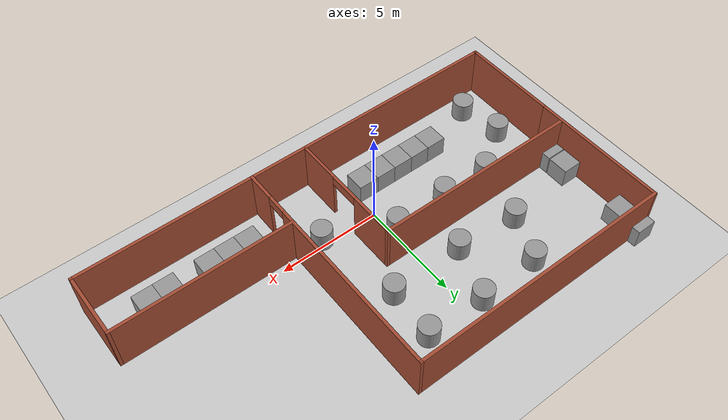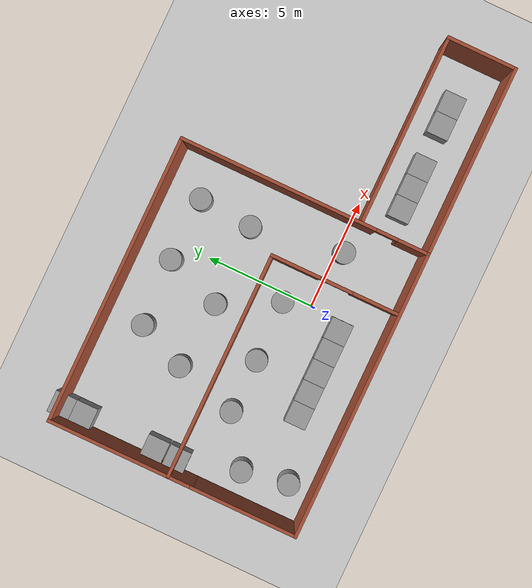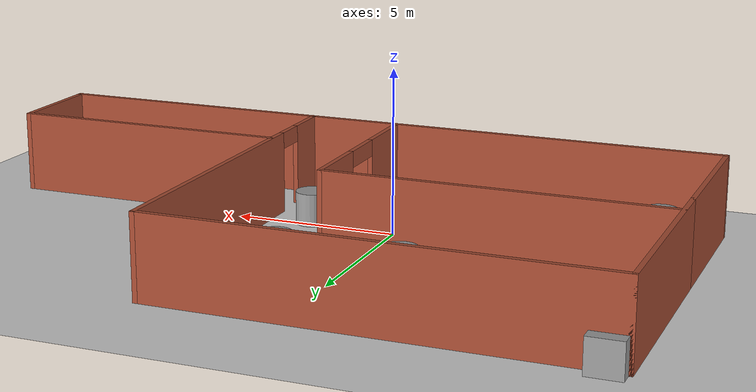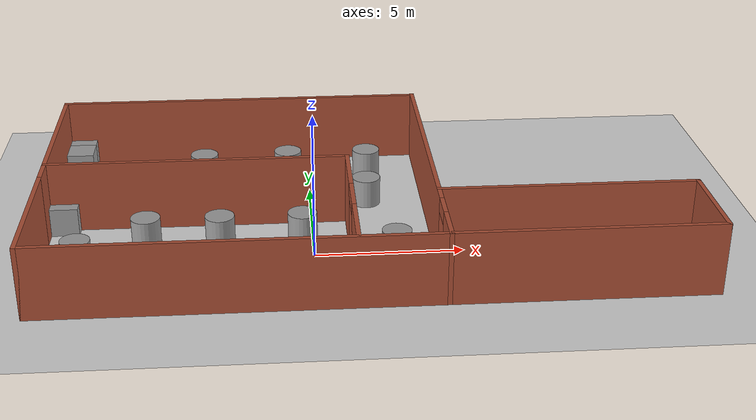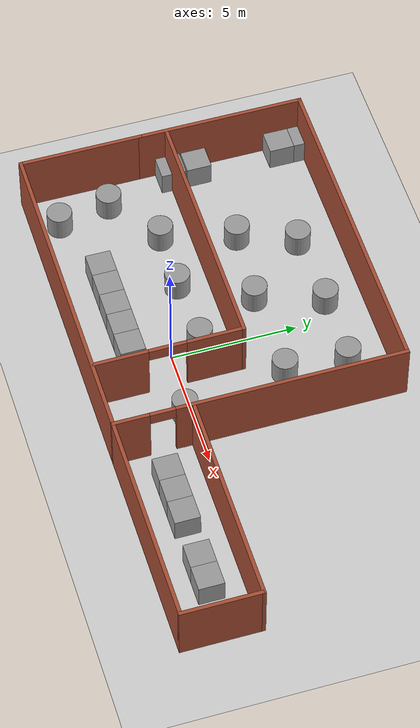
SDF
<sdf version="1.7">
 <world name="default">
  <light name="sun" type="directional">
   <pose>0 0 10 0 -0 0</pose>
   <diffuse>0.8 0.8 0.8 1</diffuse>
   <specular>0.2 0.2 0.2 1</specular>
   <attenuation>
    <range>1000</range>
    <constant>0.9</constant>
    <linear>0.01</linear>
    <quadratic>0.001</quadratic>
   </attenuation>
   <direction>-0.5 0.1 -0.9</direction>
   <spot><inner_angle>0</inner_angle><outer_angle>0</outer_angle><falloff>0</falloff></spot>
  </light>
  <model name="ground_plane">
   <static>1</static>
   <link name="link">
    <collision name="collision">
     <geometry><plane><normal>0 0 1</normal><size>100 100</size></plane></geometry>
     <surface><friction><ode><mu>100</mu><mu2>50</mu2></ode></friction></surface>
    </collision>
    <visual name="visual">
     <cast_shadows>0</cast_shadows>
     <geometry><plane><normal>0 0 1</normal><size>100 100</size></plane></geometry>
     <material>
      <script><uri>file://media/materials/scripts/gazebo.material</uri><name>Gazebo/Grey</name></script>
     </material>
    </visual>
   </link>
  </model>
  <gravity>0 0 -9.8</gravity>
  <magnetic_field>6e-06 2.3e-05 -4.2e-05</magnetic_field>
  <atmosphere type="adiabatic"/>
  <physics type="ode">
   <max_step_size>0.001</max_step_size>
   <real_time_factor>1</real_time_factor>
   <real_time_update_rate>1000</real_time_update_rate>
  </physics>
  <scene><ambient>0.4 0.4 0.4 1</ambient><background>0.7 0.7 0.7 1</background><shadows>1</shadows></scene>
  <audio><device>default</device></audio>
  <spherical_coordinates>
   <surface_model>EARTH_WGS84</surface_model>
   <latitude_deg>0</latitude_deg>
   <longitude_deg>0</longitude_deg>
   <elevation>0</elevation>
   <heading_deg>0</heading_deg>
  </spherical_coordinates>
  <model name="Simple_world">
   <link name="Wall_0">
    <pose>-4.3 -5.725 0 0 -0 0</pose>
    <visual name="Wall_0_Visual">
     <pose>0 0 1.25 0 -0 0</pose>
     <geometry><box><size>13.25 0.15 2.5</size></box></geometry>
     <material>
      <script><uri>file://media/materials/scripts/gazebo.material</uri><name>Gazebo/Bricks</name></script>
      <ambient>1 1 1 1</ambient>
      <shader type="pixel"/>
     </material>
     <meta><layer>0</layer></meta>
    </visual>
    <collision name="Wall_0_Collision">
     <pose>0 0 1.25 0 -0 0</pose>
     <geometry><box><size>13.25 0.15 2.5</size></box></geometry>
     <surface>
      <friction>
       <ode><mu>1</mu><mu2>1</mu2><fdir1>0 0 0</fdir1><slip1>0</slip1><slip2>0</slip2></ode>
       <torsional>
        <coefficient>1</coefficient>
        <patch_radius>0</patch_radius>
        <surface_radius>0</surface_radius>
        <use_patch_radius>1</use_patch_radius>
        <ode><slip>0</slip></ode>
       </torsional>
      </friction>
      <bounce><restitution_coefficient>0</restitution_coefficient><threshold>1e+06</threshold></bounce>
      <contact>
       <collide_without_contact>0</collide_without_contact>
       <collide_without_contact_bitmask>1</collide_without_contact_bitmask>
       <collide_bitmask>1</collide_bitmask>
       <ode>
        <soft_cfm>0</soft_cfm>
        <soft_erp>0.2</soft_erp>
        <kp>1e+13</kp>
        <kd>1</kd>
        <max_vel>0.01</max_vel>
        <min_depth>0</min_depth>
       </ode>
       <bullet>
        <split_impulse>1</split_impulse>
        <split_impulse_penetration_threshold>-0.01</split_impulse_penetration_threshold>
        <soft_cfm>0</soft_cfm>
        <soft_erp>0.2</soft_erp>
        <kp>1e+13</kp>
        <kd>1</kd>
       </bullet>
      </contact>
     </surface>
    </collision>
   </link>
   <link name="Wall_12">
    <pose>2.25 0 0 0 0 -1.5708</pose>
    <visual name="Wall_12_Visual_0">
     <pose>-1.24262 0 1.25 0 -0 0</pose>
     <geometry><box><size>9.11477 0.15 2.5</size></box></geometry>
     <material>
      <script><uri>file://media/materials/scripts/gazebo.material</uri><name>Gazebo/Bricks</name></script>
      <ambient>1 1 1 1</ambient>
      <shader type="pixel"/>
     </material>
     <meta><layer>0</layer></meta>
    </visual>
    <visual name="Wall_12_Visual_1">
     <pose>5.05739 0 1.25 0 -0 0</pose>
     <geometry><box><size>1.48523 0.15 2.5</size></box></geometry>
     <material>
      <script><uri>file://media/materials/scripts/gazebo.material</uri><name>Gazebo/Bricks</name></script>
      <ambient>1 1 1 1</ambient>
      <shader type="pixel"/>
     </material>
     <meta><layer>0</layer></meta>
    </visual>
    <visual name="Wall_12_Visual_2">
     <pose>3.81477 0 2.25 0 -0 0</pose>
     <geometry><box><size>1 0.15 0.5</size></box></geometry>
     <material>
      <script><uri>file://media/materials/scripts/gazebo.material</uri><name>Gazebo/Bricks</name></script>
      <ambient>1 1 1 1</ambient>
      <shader type="pixel"/>
     </material>
     <meta><layer>0</layer></meta>
    </visual>
    <collision name="Wall_12_Collision_2">
     <pose>3.81477 0 2.25 0 -0 0</pose>
     <geometry><box><size>1 0.15 0.5</size></box></geometry>
     <surface>
      <friction>
       <ode><mu>1</mu><mu2>1</mu2><fdir1>0 0 0</fdir1><slip1>0</slip1><slip2>0</slip2></ode>
       <torsional>
        <coefficient>1</coefficient>
        <patch_radius>0</patch_radius>
        <surface_radius>0</surface_radius>
        <use_patch_radius>1</use_patch_radius>
        <ode><slip>0</slip></ode>
       </torsional>
      </friction>
      <bounce><restitution_coefficient>0</restitution_coefficient><threshold>1e+06</threshold></bounce>
      <contact>
       <collide_without_contact>0</collide_without_contact>
       <collide_without_contact_bitmask>1</collide_without_contact_bitmask>
       <collide_bitmask>1</collide_bitmask>
       <ode>
        <soft_cfm>0</soft_cfm>
        <soft_erp>0.2</soft_erp>
        <kp>1e+13</kp>
        <kd>1</kd>
        <max_vel>0.01</max_vel>
        <min_depth>0</min_depth>
       </ode>
       <bullet>
        <split_impulse>1</split_impulse>
        <split_impulse_penetration_threshold>-0.01</split_impulse_penetration_threshold>
        <soft_cfm>0</soft_cfm>
        <soft_erp>0.2</soft_erp>
        <kp>1e+13</kp>
        <kd>1</kd>
       </bullet>
      </contact>
     </surface>
    </collision>
    <collision name="Wall_12_Collision_1">
     <pose>5.05739 0 1.25 0 -0 0</pose>
     <geometry><box><size>1.48523 0.15 2.5</size></box></geometry>
     <surface>
      <friction>
       <ode><mu>1</mu><mu2>1</mu2><fdir1>0 0 0</fdir1><slip1>0</slip1><slip2>0</slip2></ode>
       <torsional>
        <coefficient>1</coefficient>
        <patch_radius>0</patch_radius>
        <surface_radius>0</surface_radius>
        <use_patch_radius>1</use_patch_radius>
        <ode><slip>0</slip></ode>
       </torsional>
      </friction>
      <bounce><restitution_coefficient>0</restitution_coefficient><threshold>1e+06</threshold></bounce>
      <contact>
       <collide_without_contact>0</collide_without_contact>
       <collide_without_contact_bitmask>1</collide_without_contact_bitmask>
       <collide_bitmask>1</collide_bitmask>
       <ode>
        <soft_cfm>0</soft_cfm>
        <soft_erp>0.2</soft_erp>
        <kp>1e+13</kp>
        <kd>1</kd>
        <max_vel>0.01</max_vel>
        <min_depth>0</min_depth>
       </ode>
       <bullet>
        <split_impulse>1</split_impulse>
        <split_impulse_penetration_threshold>-0.01</split_impulse_penetration_threshold>
        <soft_cfm>0</soft_cfm>
        <soft_erp>0.2</soft_erp>
        <kp>1e+13</kp>
        <kd>1</kd>
       </bullet>
      </contact>
     </surface>
    </collision>
    <collision name="Wall_12_Collision_0">
     <pose>-1.24262 0 1.25 0 -0 0</pose>
     <geometry><box><size>9.11477 0.15 2.5</size></box></geometry>
     <surface>
      <friction>
       <ode><mu>1</mu><mu2>1</mu2><fdir1>0 0 0</fdir1><slip1>0</slip1><slip2>0</slip2></ode>
       <torsional>
        <coefficient>1</coefficient>
        <patch_radius>0</patch_radius>
        <surface_radius>0</surface_radius>
        <use_patch_radius>1</use_patch_radius>
        <ode><slip>0</slip></ode>
       </torsional>
      </friction>
      <bounce><restitution_coefficient>0</restitution_coefficient><threshold>1e+06</threshold></bounce>
      <contact>
       <collide_without_contact>0</collide_without_contact>
       <collide_without_contact_bitmask>1</collide_without_contact_bitmask>
       <collide_bitmask>1</collide_bitmask>
       <ode>
        <soft_cfm>0</soft_cfm>
        <soft_erp>0.2</soft_erp>
        <kp>1e+13</kp>
        <kd>1</kd>
        <max_vel>0.01</max_vel>
        <min_depth>0</min_depth>
       </ode>
       <bullet>
        <split_impulse>1</split_impulse>
        <split_impulse_penetration_threshold>-0.01</split_impulse_penetration_threshold>
        <soft_cfm>0</soft_cfm>
        <soft_erp>0.2</soft_erp>
        <kp>1e+13</kp>
        <kd>1</kd>
       </bullet>
      </contact>
     </surface>
    </collision>
   </link>
   <link name="Wall_13">
    <pose>6.55 -5.725 0 0 -0 0</pose>
    <visual name="Wall_13_Visual">
     <pose>0 0 1.25 0 -0 0</pose>
     <geometry><box><size>8.75 0.15 2.5</size></box></geometry>
     <material>
      <script><uri>file://media/materials/scripts/gazebo.material</uri><name>Gazebo/Bricks</name></script>
      <ambient>1 1 1 1</ambient>
      <shader type="pixel"/>
     </material>
     <meta><layer>0</layer></meta>
    </visual>
    <collision name="Wall_13_Collision">
     <pose>0 0 1.25 0 -0 0</pose>
     <geometry><box><size>8.75 0.15 2.5</size></box></geometry>
     <surface>
      <friction>
       <ode><mu>1</mu><mu2>1</mu2><fdir1>0 0 0</fdir1><slip1>0</slip1><slip2>0</slip2></ode>
       <torsional>
        <coefficient>1</coefficient>
        <patch_radius>0</patch_radius>
        <surface_radius>0</surface_radius>
        <use_patch_radius>1</use_patch_radius>
        <ode><slip>0</slip></ode>
       </torsional>
      </friction>
      <bounce><restitution_coefficient>0</restitution_coefficient><threshold>1e+06</threshold></bounce>
      <contact>
       <collide_without_contact>0</collide_without_contact>
       <collide_without_contact_bitmask>1</collide_without_contact_bitmask>
       <collide_bitmask>1</collide_bitmask>
       <ode>
        <soft_cfm>0</soft_cfm>
        <soft_erp>0.2</soft_erp>
        <kp>1e+13</kp>
        <kd>1</kd>
        <max_vel>0.01</max_vel>
        <min_depth>0</min_depth>
       </ode>
       <bullet>
        <split_impulse>1</split_impulse>
        <split_impulse_penetration_threshold>-0.01</split_impulse_penetration_threshold>
        <soft_cfm>0</soft_cfm>
        <soft_erp>0.2</soft_erp>
        <kp>1e+13</kp>
        <kd>1</kd>
       </bullet>
      </contact>
     </surface>
    </collision>
   </link>
   <link name="Wall_14">
    <pose>10.85 -4.175 0 0 -0 1.5708</pose>
    <visual name="Wall_14_Visual">
     <pose>0 0 1.25 0 -0 0</pose>
     <geometry><box><size>3.25 0.15 2.5</size></box></geometry>
     <material>
      <script><uri>file://media/materials/scripts/gazebo.material</uri><name>Gazebo/Bricks</name></script>
      <ambient>1 1 1 1</ambient>
      <shader type="pixel"/>
     </material>
     <meta><layer>0</layer></meta>
    </visual>
    <collision name="Wall_14_Collision">
     <pose>0 0 1.25 0 -0 0</pose>
     <geometry><box><size>3.25 0.15 2.5</size></box></geometry>
     <surface>
      <friction>
       <ode><mu>1</mu><mu2>1</mu2><fdir1>0 0 0</fdir1><slip1>0</slip1><slip2>0</slip2></ode>
       <torsional>
        <coefficient>1</coefficient>
        <patch_radius>0</patch_radius>
        <surface_radius>0</surface_radius>
        <use_patch_radius>1</use_patch_radius>
        <ode><slip>0</slip></ode>
       </torsional>
      </friction>
      <bounce><restitution_coefficient>0</restitution_coefficient><threshold>1e+06</threshold></bounce>
      <contact>
       <collide_without_contact>0</collide_without_contact>
       <collide_without_contact_bitmask>1</collide_without_contact_bitmask>
       <collide_bitmask>1</collide_bitmask>
       <ode>
        <soft_cfm>0</soft_cfm>
        <soft_erp>0.2</soft_erp>
        <kp>1e+13</kp>
        <kd>1</kd>
        <max_vel>0.01</max_vel>
        <min_depth>0</min_depth>
       </ode>
       <bullet>
        <split_impulse>1</split_impulse>
        <split_impulse_penetration_threshold>-0.01</split_impulse_penetration_threshold>
        <soft_cfm>0</soft_cfm>
        <soft_erp>0.2</soft_erp>
        <kp>1e+13</kp>
        <kd>1</kd>
       </bullet>
      </contact>
     </surface>
    </collision>
   </link>
   <link name="Wall_15">
    <pose>6.55 -2.625 0 0 -0 3.14159</pose>
    <visual name="Wall_15_Visual">
     <pose>0 0 1.25 0 -0 0</pose>
     <geometry><box><size>8.75 0.15 2.5</size></box></geometry>
     <material>
      <script><uri>file://media/materials/scripts/gazebo.material</uri><name>Gazebo/Bricks</name></script>
      <ambient>1 1 1 1</ambient>
      <shader type="pixel"/>
     </material>
     <meta><layer>0</layer></meta>
    </visual>
    <collision name="Wall_15_Collision">
     <pose>0 0 1.25 0 -0 0</pose>
     <geometry><box><size>8.75 0.15 2.5</size></box></geometry>
     <surface>
      <friction>
       <ode><mu>1</mu><mu2>1</mu2><fdir1>0 0 0</fdir1><slip1>0</slip1><slip2>0</slip2></ode>
       <torsional>
        <coefficient>1</coefficient>
        <patch_radius>0</patch_radius>
        <surface_radius>0</surface_radius>
        <use_patch_radius>1</use_patch_radius>
        <ode><slip>0</slip></ode>
       </torsional>
      </friction>
      <bounce><restitution_coefficient>0</restitution_coefficient><threshold>1e+06</threshold></bounce>
      <contact>
       <collide_without_contact>0</collide_without_contact>
       <collide_without_contact_bitmask>1</collide_without_contact_bitmask>
       <collide_bitmask>1</collide_bitmask>
       <ode>
        <soft_cfm>0</soft_cfm>
        <soft_erp>0.2</soft_erp>
        <kp>1e+13</kp>
        <kd>1</kd>
        <max_vel>0.01</max_vel>
        <min_depth>0</min_depth>
       </ode>
       <bullet>
        <split_impulse>1</split_impulse>
        <split_impulse_penetration_threshold>-0.01</split_impulse_penetration_threshold>
        <soft_cfm>0</soft_cfm>
        <soft_erp>0.2</soft_erp>
        <kp>1e+13</kp>
        <kd>1</kd>
       </bullet>
      </contact>
     </surface>
    </collision>
   </link>
   <link name="Wall_18">
    <pose>-0.579032 -2.72339 0 0 -0 1.5708</pose>
    <visual name="Wall_18_Visual_1">
     <pose>1.84221 0 1.25 0 -0 0</pose>
     <geometry><box><size>2.31559 0.15 2.5</size></box></geometry>
     <material>
      <script><uri>file://media/materials/scripts/gazebo.material</uri><name>Gazebo/Bricks</name></script>
      <ambient>1 1 1 1</ambient>
      <shader type="pixel"/>
     </material>
     <meta><layer>0</layer></meta>
    </visual>
    <visual name="Wall_18_Visual_2">
     <pose>-0.065589 0 2.25 0 -0 0</pose>
     <geometry><box><size>1.5 0.15 0.5</size></box></geometry>
     <material>
      <script><uri>file://media/materials/scripts/gazebo.material</uri><name>Gazebo/Bricks</name></script>
      <ambient>1 1 1 1</ambient>
      <shader type="pixel"/>
     </material>
     <meta><layer>0</layer></meta>
    </visual>
    <visual name="Wall_18_Visual_0">
     <pose>-1.90779 0 1.25 0 -0 0</pose>
     <geometry><box><size>2.18441 0.15 2.5</size></box></geometry>
     <material>
      <script><uri>file://media/materials/scripts/gazebo.material</uri><name>Gazebo/Bricks</name></script>
      <ambient>1 1 1 1</ambient>
      <shader type="pixel"/>
     </material>
     <meta><layer>0</layer></meta>
    </visual>
    <collision name="Wall_18_Collision_1">
     <pose>1.84221 0 1.25 0 -0 0</pose>
     <geometry><box><size>2.31559 0.15 2.5</size></box></geometry>
     <surface>
      <friction>
       <ode><mu>1</mu><mu2>1</mu2><fdir1>0 0 0</fdir1><slip1>0</slip1><slip2>0</slip2></ode>
       <torsional>
        <coefficient>1</coefficient>
        <patch_radius>0</patch_radius>
        <surface_radius>0</surface_radius>
        <use_patch_radius>1</use_patch_radius>
        <ode><slip>0</slip></ode>
       </torsional>
      </friction>
      <bounce><restitution_coefficient>0</restitution_coefficient><threshold>1e+06</threshold></bounce>
      <contact>
       <collide_without_contact>0</collide_without_contact>
       <collide_without_contact_bitmask>1</collide_without_contact_bitmask>
       <collide_bitmask>1</collide_bitmask>
       <ode>
        <soft_cfm>0</soft_cfm>
        <soft_erp>0.2</soft_erp>
        <kp>1e+13</kp>
        <kd>1</kd>
        <max_vel>0.01</max_vel>
        <min_depth>0</min_depth>
       </ode>
       <bullet>
        <split_impulse>1</split_impulse>
        <split_impulse_penetration_threshold>-0.01</split_impulse_penetration_threshold>
        <soft_cfm>0</soft_cfm>
        <soft_erp>0.2</soft_erp>
        <kp>1e+13</kp>
        <kd>1</kd>
       </bullet>
      </contact>
     </surface>
    </collision>
    <collision name="Wall_18_Collision_2">
     <pose>-0.065589 0 2.25 0 -0 0</pose>
     <geometry><box><size>1.5 0.15 0.5</size></box></geometry>
     <surface>
      <friction>
       <ode><mu>1</mu><mu2>1</mu2><fdir1>0 0 0</fdir1><slip1>0</slip1><slip2>0</slip2></ode>
       <torsional>
        <coefficient>1</coefficient>
        <patch_radius>0</patch_radius>
        <surface_radius>0</surface_radius>
        <use_patch_radius>1</use_patch_radius>
        <ode><slip>0</slip></ode>
       </torsional>
      </friction>
      <bounce><restitution_coefficient>0</restitution_coefficient><threshold>1e+06</threshold></bounce>
      <contact>
       <collide_without_contact>0</collide_without_contact>
       <collide_without_contact_bitmask>1</collide_without_contact_bitmask>
       <collide_bitmask>1</collide_bitmask>
       <ode>
        <soft_cfm>0</soft_cfm>
        <soft_erp>0.2</soft_erp>
        <kp>1e+13</kp>
        <kd>1</kd>
        <max_vel>0.01</max_vel>
        <min_depth>0</min_depth>
       </ode>
       <bullet>
        <split_impulse>1</split_impulse>
        <split_impulse_penetration_threshold>-0.01</split_impulse_penetration_threshold>
        <soft_cfm>0</soft_cfm>
        <soft_erp>0.2</soft_erp>
        <kp>1e+13</kp>
        <kd>1</kd>
       </bullet>
      </contact>
     </surface>
    </collision>
    <collision name="Wall_18_Collision_0">
     <pose>-1.90779 0 1.25 0 -0 0</pose>
     <geometry><box><size>2.18441 0.15 2.5</size></box></geometry>
     <surface>
      <friction>
       <ode><mu>1</mu><mu2>1</mu2><fdir1>0 0 0</fdir1><slip1>0</slip1><slip2>0</slip2></ode>
       <torsional>
        <coefficient>1</coefficient>
        <patch_radius>0</patch_radius>
        <surface_radius>0</surface_radius>
        <use_patch_radius>1</use_patch_radius>
        <ode><slip>0</slip></ode>
       </torsional>
      </friction>
      <bounce><restitution_coefficient>0</restitution_coefficient><threshold>1e+06</threshold></bounce>
      <contact>
       <collide_without_contact>0</collide_without_contact>
       <collide_without_contact_bitmask>1</collide_without_contact_bitmask>
       <collide_bitmask>1</collide_bitmask>
       <ode>
        <soft_cfm>0</soft_cfm>
        <soft_erp>0.2</soft_erp>
        <kp>1e+13</kp>
        <kd>1</kd>
        <max_vel>0.01</max_vel>
        <min_depth>0</min_depth>
       </ode>
       <bullet>
        <split_impulse>1</split_impulse>
        <split_impulse_penetration_threshold>-0.01</split_impulse_penetration_threshold>
        <soft_cfm>0</soft_cfm>
        <soft_erp>0.2</soft_erp>
        <kp>1e+13</kp>
        <kd>1</kd>
       </bullet>
      </contact>
     </surface>
    </collision>
   </link>
   <link name="Wall_19">
    <pose>-5.70403 0.201612 0 0 -0 3.14159</pose>
    <visual name="Wall_19_Visual">
     <pose>0 0 1.25 0 -0 0</pose>
     <geometry><box><size>10.4 0.15 2.5</size></box></geometry>
     <material>
      <script><uri>file://media/materials/scripts/gazebo.material</uri><name>Gazebo/Bricks</name></script>
      <ambient>1 1 1 1</ambient>
      <shader type="pixel"/>
     </material>
     <meta><layer>0</layer></meta>
    </visual>
    <collision name="Wall_19_Collision">
     <pose>0 0 1.25 0 -0 0</pose>
     <geometry><box><size>10.4 0.15 2.5</size></box></geometry>
     <surface>
      <friction>
       <ode><mu>1</mu><mu2>1</mu2><fdir1>0 0 0</fdir1><slip1>0</slip1><slip2>0</slip2></ode>
       <torsional>
        <coefficient>1</coefficient>
        <patch_radius>0</patch_radius>
        <surface_radius>0</surface_radius>
        <use_patch_radius>1</use_patch_radius>
        <ode><slip>0</slip></ode>
       </torsional>
      </friction>
      <bounce><restitution_coefficient>0</restitution_coefficient><threshold>1e+06</threshold></bounce>
      <contact>
       <collide_without_contact>0</collide_without_contact>
       <collide_without_contact_bitmask>1</collide_without_contact_bitmask>
       <collide_bitmask>1</collide_bitmask>
       <ode>
        <soft_cfm>0</soft_cfm>
        <soft_erp>0.2</soft_erp>
        <kp>1e+13</kp>
        <kd>1</kd>
        <max_vel>0.01</max_vel>
        <min_depth>0</min_depth>
       </ode>
       <bullet>
        <split_impulse>1</split_impulse>
        <split_impulse_penetration_threshold>-0.01</split_impulse_penetration_threshold>
        <soft_cfm>0</soft_cfm>
        <soft_erp>0.2</soft_erp>
        <kp>1e+13</kp>
        <kd>1</kd>
       </bullet>
      </contact>
     </surface>
    </collision>
   </link>
   <link name="Wall_2">
    <pose>-10.85 -3.3 0 0 -0 1.5708</pose>
    <visual name="Wall_2_Visual">
     <pose>0 0 1.25 0 -0 0</pose>
     <geometry><box><size>5 0.15 2.5</size></box></geometry>
     <material>
      <script><uri>file://media/materials/scripts/gazebo.material</uri><name>Gazebo/Bricks</name></script>
      <ambient>1 1 1 1</ambient>
      <shader type="pixel"/>
     </material>
     <meta><layer>0</layer></meta>
    </visual>
    <collision name="Wall_2_Collision">
     <pose>0 0 1.25 0 -0 0</pose>
     <geometry><box><size>5 0.15 2.5</size></box></geometry>
     <surface>
      <friction>
       <ode><mu>1</mu><mu2>1</mu2><fdir1>0 0 0</fdir1><slip1>0</slip1><slip2>0</slip2></ode>
       <torsional>
        <coefficient>1</coefficient>
        <patch_radius>0</patch_radius>
        <surface_radius>0</surface_radius>
        <use_patch_radius>1</use_patch_radius>
        <ode><slip>0</slip></ode>
       </torsional>
      </friction>
      <bounce><restitution_coefficient>0</restitution_coefficient><threshold>1e+06</threshold></bounce>
      <contact>
       <collide_without_contact>0</collide_without_contact>
       <collide_without_contact_bitmask>1</collide_without_contact_bitmask>
       <collide_bitmask>1</collide_bitmask>
       <ode>
        <soft_cfm>0</soft_cfm>
        <soft_erp>0.2</soft_erp>
        <kp>1e+13</kp>
        <kd>1</kd>
        <max_vel>0.01</max_vel>
        <min_depth>0</min_depth>
       </ode>
       <bullet>
        <split_impulse>1</split_impulse>
        <split_impulse_penetration_threshold>-0.01</split_impulse_penetration_threshold>
        <soft_cfm>0</soft_cfm>
        <soft_erp>0.2</soft_erp>
        <kp>1e+13</kp>
        <kd>1</kd>
       </bullet>
      </contact>
     </surface>
    </collision>
   </link>
   <link name="Wall_6">
    <pose>-10.85 2.425 0 0 -0 1.5708</pose>
    <visual name="Wall_6_Visual">
     <pose>0 0 1.25 0 -0 0</pose>
     <geometry><box><size>6.75 0.15 2.5</size></box></geometry>
     <material>
      <script><uri>file://media/materials/scripts/gazebo.material</uri><name>Gazebo/Bricks</name></script>
      <ambient>1 1 1 1</ambient>
      <shader type="pixel"/>
     </material>
     <meta><layer>0</layer></meta>
    </visual>
    <collision name="Wall_6_Collision">
     <pose>0 0 1.25 0 -0 0</pose>
     <geometry><box><size>6.75 0.15 2.5</size></box></geometry>
     <surface>
      <friction>
       <ode><mu>1</mu><mu2>1</mu2><fdir1>0 0 0</fdir1><slip1>0</slip1><slip2>0</slip2></ode>
       <torsional>
        <coefficient>1</coefficient>
        <patch_radius>0</patch_radius>
        <surface_radius>0</surface_radius>
        <use_patch_radius>1</use_patch_radius>
        <ode><slip>0</slip></ode>
       </torsional>
      </friction>
      <bounce><restitution_coefficient>0</restitution_coefficient><threshold>1e+06</threshold></bounce>
      <contact>
       <collide_without_contact>0</collide_without_contact>
       <collide_without_contact_bitmask>1</collide_without_contact_bitmask>
       <collide_bitmask>1</collide_bitmask>
       <ode>
        <soft_cfm>0</soft_cfm>
        <soft_erp>0.2</soft_erp>
        <kp>1e+13</kp>
        <kd>1</kd>
        <max_vel>0.01</max_vel>
        <min_depth>0</min_depth>
       </ode>
       <bullet>
        <split_impulse>1</split_impulse>
        <split_impulse_penetration_threshold>-0.01</split_impulse_penetration_threshold>
        <soft_cfm>0</soft_cfm>
        <soft_erp>0.2</soft_erp>
        <kp>1e+13</kp>
        <kd>1</kd>
       </bullet>
      </contact>
     </surface>
    </collision>
   </link>
   <link name="Wall_7">
    <pose>-4.3 5.725 0 0 -0 0</pose>
    <visual name="Wall_7_Visual">
     <pose>0 0 1.25 0 -0 0</pose>
     <geometry><box><size>13.25 0.15 2.5</size></box></geometry>
     <material>
      <script><uri>file://media/materials/scripts/gazebo.material</uri><name>Gazebo/Bricks</name></script>
      <ambient>1 1 1 1</ambient>
      <shader type="pixel"/>
     </material>
     <meta><layer>0</layer></meta>
    </visual>
    <collision name="Wall_7_Collision">
     <pose>0 0 1.25 0 -0 0</pose>
     <geometry><box><size>13.25 0.15 2.5</size></box></geometry>
     <surface>
      <friction>
       <ode><mu>1</mu><mu2>1</mu2><fdir1>0 0 0</fdir1><slip1>0</slip1><slip2>0</slip2></ode>
       <torsional>
        <coefficient>1</coefficient>
        <patch_radius>0</patch_radius>
        <surface_radius>0</surface_radius>
        <use_patch_radius>1</use_patch_radius>
        <ode><slip>0</slip></ode>
       </torsional>
      </friction>
      <bounce><restitution_coefficient>0</restitution_coefficient><threshold>1e+06</threshold></bounce>
      <contact>
       <collide_without_contact>0</collide_without_contact>
       <collide_without_contact_bitmask>1</collide_without_contact_bitmask>
       <collide_bitmask>1</collide_bitmask>
       <ode>
        <soft_cfm>0</soft_cfm>
        <soft_erp>0.2</soft_erp>
        <kp>1e+13</kp>
        <kd>1</kd>
        <max_vel>0.01</max_vel>
        <min_depth>0</min_depth>
       </ode>
       <bullet>
        <split_impulse>1</split_impulse>
        <split_impulse_penetration_threshold>-0.01</split_impulse_penetration_threshold>
        <soft_cfm>0</soft_cfm>
        <soft_erp>0.2</soft_erp>
        <kp>1e+13</kp>
        <kd>1</kd>
       </bullet>
      </contact>
     </surface>
    </collision>
   </link>
   <static>1</static>
   <pose>1.81774 2.29441 0 0 -0 0</pose>
  </model>
  <light name="user_point_light_0" type="point">
   <pose>-2.43968 3.40055 1 0 -0 0</pose>
   <diffuse>0.5 0.5 0.5 1</diffuse>
   <specular>0.1 0.1 0.1 1</specular>
   <attenuation>
    <range>20</range>
    <constant>0.5</constant>
    <linear>0.01</linear>
    <quadratic>0.001</quadratic>
   </attenuation>
   <cast_shadows>0</cast_shadows>
   <direction>0 0 -1</direction>
  </light>
  <light name="user_point_light_1" type="point">
   <pose>-3.3024 -2.32787 1 0 -0 0</pose>
   <diffuse>0.5 0.5 0.5 1</diffuse>
   <specular>0.1 0.1 0.1 1</specular>
   <attenuation>
    <range>20</range>
    <constant>0.5</constant>
    <linear>0.01</linear>
    <quadratic>0.001</quadratic>
   </attenuation>
   <cast_shadows>0</cast_shadows>
   <direction>0 0 -1</direction>
  </light>
  <light name="user_point_light_2" type="point">
   <pose>8.62158 -3.60923 1 0 -0 0</pose>
   <diffuse>0.5 0.5 0.5 1</diffuse>
   <specular>0.1 0.1 0.1 1</specular>
   <attenuation>
    <range>20</range>
    <constant>0.5</constant>
    <linear>0.01</linear>
    <quadratic>0.001</quadratic>
   </attenuation>
   <cast_shadows>0</cast_shadows>
   <direction>0 0 -1</direction>
  </light>
  <model name="Simple_model">
   <link name="link_10">
    <inertial>
     <mass>100</mass>
     <inertia><ixx>16.6667</ixx><ixy>0</ixy><ixz>0</ixz><iyy>16.6667</iyy><iyz>0</iyz><izz>16.6667</izz></inertia>
    </inertial>
    <pose>-2.5 -3.5 0.5 0 -0 0</pose>
    <visual name="visual">
     <geometry><box><size>1 1 1</size></box></geometry>
     <material>
      <lighting>1</lighting>
      <script><uri>file://media/materials/scripts/gazebo.material</uri><name>Gazebo/Grey</name></script>
      <shader type="pixel"><normal_map>__default__</normal_map></shader>
      <ambient>0.3 0.3 0.3 1</ambient>
      <diffuse>0.7 0.7 0.7 1</diffuse>
      <specular>0.01 0.01 0.01 1</specular>
      <emissive>0 0 0 1</emissive>
     </material>
    </visual>
    <collision name="collision">
     <geometry><box><size>1 1 1</size></box></geometry>
     <surface>
      <friction>
       <ode><mu>1</mu><mu2>1</mu2><fdir1>0 0 0</fdir1><slip1>0</slip1><slip2>0</slip2></ode>
       <torsional>
        <coefficient>1</coefficient>
        <patch_radius>0</patch_radius>
        <surface_radius>0</surface_radius>
        <use_patch_radius>1</use_patch_radius>
        <ode><slip>0</slip></ode>
       </torsional>
      </friction>
      <bounce><restitution_coefficient>0</restitution_coefficient><threshold>1e+06</threshold></bounce>
      <contact>
       <collide_without_contact>0</collide_without_contact>
       <collide_without_contact_bitmask>1</collide_without_contact_bitmask>
       <collide_bitmask>1</collide_bitmask>
       <ode>
        <soft_cfm>0</soft_cfm>
        <soft_erp>0.2</soft_erp>
        <kp>1e+13</kp>
        <kd>1</kd>
        <max_vel>0.01</max_vel>
        <min_depth>0</min_depth>
       </ode>
       <bullet>
        <split_impulse>1</split_impulse>
        <split_impulse_penetration_threshold>-0.01</split_impulse_penetration_threshold>
        <soft_cfm>0</soft_cfm>
        <soft_erp>0.2</soft_erp>
        <kp>1e+13</kp>
        <kd>1</kd>
       </bullet>
      </contact>
     </surface>
    </collision>
   </link>
   <link name="link_11">
    <inertial>
     <mass>100</mass>
     <inertia><ixx>16.6667</ixx><ixy>0</ixy><ixz>0</ixz><iyy>16.6667</iyy><iyz>0</iyz><izz>16.6667</izz></inertia>
    </inertial>
    <pose>-3.5 -3.5 0.5 0 -0 0</pose>
    <visual name="visual">
     <geometry><box><size>1 1 1</size></box></geometry>
     <material>
      <lighting>1</lighting>
      <script><uri>file://media/materials/scripts/gazebo.material</uri><name>Gazebo/Grey</name></script>
      <shader type="pixel"><normal_map>__default__</normal_map></shader>
      <ambient>0.3 0.3 0.3 1</ambient>
      <diffuse>0.7 0.7 0.7 1</diffuse>
      <specular>0.01 0.01 0.01 1</specular>
      <emissive>0 0 0 1</emissive>
     </material>
    </visual>
    <collision name="collision">
     <geometry><box><size>1 1 1</size></box></geometry>
     <surface>
      <friction>
       <ode><mu>1</mu><mu2>1</mu2><fdir1>0 0 0</fdir1><slip1>0</slip1><slip2>0</slip2></ode>
       <torsional>
        <coefficient>1</coefficient>
        <patch_radius>0</patch_radius>
        <surface_radius>0</surface_radius>
        <use_patch_radius>1</use_patch_radius>
        <ode><slip>0</slip></ode>
       </torsional>
      </friction>
      <bounce><restitution_coefficient>0</restitution_coefficient><threshold>1e+06</threshold></bounce>
      <contact>
       <collide_without_contact>0</collide_without_contact>
       <collide_without_contact_bitmask>1</collide_without_contact_bitmask>
       <collide_bitmask>1</collide_bitmask>
       <ode>
        <soft_cfm>0</soft_cfm>
        <soft_erp>0.2</soft_erp>
        <kp>1e+13</kp>
        <kd>1</kd>
        <max_vel>0.01</max_vel>
        <min_depth>0</min_depth>
       </ode>
       <bullet>
        <split_impulse>1</split_impulse>
        <split_impulse_penetration_threshold>-0.01</split_impulse_penetration_threshold>
        <soft_cfm>0</soft_cfm>
        <soft_erp>0.2</soft_erp>
        <kp>1e+13</kp>
        <kd>1</kd>
       </bullet>
      </contact>
     </surface>
    </collision>
   </link>
   <link name="link_12">
    <inertial>
     <mass>100</mass>
     <inertia><ixx>16.6667</ixx><ixy>0</ixy><ixz>0</ixz><iyy>16.6667</iyy><iyz>0</iyz><izz>16.6667</izz></inertia>
    </inertial>
    <pose>-4.5 -3.5 0.5 0 -0 0</pose>
    <visual name="visual">
     <geometry><box><size>1 1 1</size></box></geometry>
     <material>
      <lighting>1</lighting>
      <script><uri>file://media/materials/scripts/gazebo.material</uri><name>Gazebo/Grey</name></script>
      <shader type="pixel"><normal_map>__default__</normal_map></shader>
      <ambient>0.3 0.3 0.3 1</ambient>
      <diffuse>0.7 0.7 0.7 1</diffuse>
      <specular>0.01 0.01 0.01 1</specular>
      <emissive>0 0 0 1</emissive>
     </material>
    </visual>
    <collision name="collision">
     <geometry><box><size>1 1 1</size></box></geometry>
     <surface>
      <friction>
       <ode><mu>1</mu><mu2>1</mu2><fdir1>0 0 0</fdir1><slip1>0</slip1><slip2>0</slip2></ode>
       <torsional>
        <coefficient>1</coefficient>
        <patch_radius>0</patch_radius>
        <surface_radius>0</surface_radius>
        <use_patch_radius>1</use_patch_radius>
        <ode><slip>0</slip></ode>
       </torsional>
      </friction>
      <bounce><restitution_coefficient>0</restitution_coefficient><threshold>1e+06</threshold></bounce>
      <contact>
       <collide_without_contact>0</collide_without_contact>
       <collide_without_contact_bitmask>1</collide_without_contact_bitmask>
       <collide_bitmask>1</collide_bitmask>
       <ode>
        <soft_cfm>0</soft_cfm>
        <soft_erp>0.2</soft_erp>
        <kp>1e+13</kp>
        <kd>1</kd>
        <max_vel>0.01</max_vel>
        <min_depth>0</min_depth>
       </ode>
       <bullet>
        <split_impulse>1</split_impulse>
        <split_impulse_penetration_threshold>-0.01</split_impulse_penetration_threshold>
        <soft_cfm>0</soft_cfm>
        <soft_erp>0.2</soft_erp>
        <kp>1e+13</kp>
        <kd>1</kd>
       </bullet>
      </contact>
     </surface>
    </collision>
   </link>
   <link name="link_13">
    <inertial>
     <mass>100</mass>
     <inertia><ixx>16.6667</ixx><ixy>0</ixy><ixz>0</ixz><iyy>16.6667</iyy><iyz>0</iyz><izz>16.6667</izz></inertia>
    </inertial>
    <pose>5.5 -3.75 0.5 0 -0 0</pose>
    <visual name="visual">
     <geometry><box><size>1 1 1</size></box></geometry>
     <material>
      <lighting>1</lighting>
      <script><uri>file://media/materials/scripts/gazebo.material</uri><name>Gazebo/Grey</name></script>
      <shader type="pixel"><normal_map>__default__</normal_map></shader>
      <ambient>0.3 0.3 0.3 1</ambient>
      <diffuse>0.7 0.7 0.7 1</diffuse>
      <specular>0.01 0.01 0.01 1</specular>
      <emissive>0 0 0 1</emissive>
     </material>
    </visual>
    <collision name="collision">
     <geometry><box><size>1 1 1</size></box></geometry>
     <surface>
      <friction>
       <ode><mu>1</mu><mu2>1</mu2><fdir1>0 0 0</fdir1><slip1>0</slip1><slip2>0</slip2></ode>
       <torsional>
        <coefficient>1</coefficient>
        <patch_radius>0</patch_radius>
        <surface_radius>0</surface_radius>
        <use_patch_radius>1</use_patch_radius>
        <ode><slip>0</slip></ode>
       </torsional>
      </friction>
      <bounce><restitution_coefficient>0</restitution_coefficient><threshold>1e+06</threshold></bounce>
      <contact>
       <collide_without_contact>0</collide_without_contact>
       <collide_without_contact_bitmask>1</collide_without_contact_bitmask>
       <collide_bitmask>1</collide_bitmask>
       <ode>
        <soft_cfm>0</soft_cfm>
        <soft_erp>0.2</soft_erp>
        <kp>1e+13</kp>
        <kd>1</kd>
        <max_vel>0.01</max_vel>
        <min_depth>0</min_depth>
       </ode>
       <bullet>
        <split_impulse>1</split_impulse>
        <split_impulse_penetration_threshold>-0.01</split_impulse_penetration_threshold>
        <soft_cfm>0</soft_cfm>
        <soft_erp>0.2</soft_erp>
        <kp>1e+13</kp>
        <kd>1</kd>
       </bullet>
      </contact>
     </surface>
    </collision>
   </link>
   <link name="link_13_clone">
    <inertial>
     <mass>100</mass>
     <inertia><ixx>16.6667</ixx><ixy>0</ixy><ixz>0</ixz><iyy>16.6667</iyy><iyz>0</iyz><izz>16.6667</izz></inertia>
    </inertial>
    <pose>6.5 -3.75 0.5 0 -0 0</pose>
    <visual name="visual">
     <geometry><box><size>1 1 1</size></box></geometry>
     <material>
      <lighting>1</lighting>
      <script><uri>file://media/materials/scripts/gazebo.material</uri><name>Gazebo/Grey</name></script>
      <shader type="pixel"><normal_map>__default__</normal_map></shader>
      <ambient>0.3 0.3 0.3 1</ambient>
      <diffuse>0.7 0.7 0.7 1</diffuse>
      <specular>0.01 0.01 0.01 1</specular>
      <emissive>0 0 0 1</emissive>
     </material>
    </visual>
    <collision name="collision">
     <geometry><box><size>1 1 1</size></box></geometry>
     <surface>
      <friction>
       <ode><mu>1</mu><mu2>1</mu2><fdir1>0 0 0</fdir1><slip1>0</slip1><slip2>0</slip2></ode>
       <torsional>
        <coefficient>1</coefficient>
        <patch_radius>0</patch_radius>
        <surface_radius>0</surface_radius>
        <use_patch_radius>1</use_patch_radius>
        <ode><slip>0</slip></ode>
       </torsional>
      </friction>
      <bounce><restitution_coefficient>0</restitution_coefficient><threshold>1e+06</threshold></bounce>
      <contact>
       <collide_without_contact>0</collide_without_contact>
       <collide_without_contact_bitmask>1</collide_without_contact_bitmask>
       <collide_bitmask>1</collide_bitmask>
       <ode>
        <soft_cfm>0</soft_cfm>
        <soft_erp>0.2</soft_erp>
        <kp>1e+13</kp>
        <kd>1</kd>
        <max_vel>0.01</max_vel>
        <min_depth>0</min_depth>
       </ode>
       <bullet>
        <split_impulse>1</split_impulse>
        <split_impulse_penetration_threshold>-0.01</split_impulse_penetration_threshold>
        <soft_cfm>0</soft_cfm>
        <soft_erp>0.2</soft_erp>
        <kp>1e+13</kp>
        <kd>1</kd>
       </bullet>
      </contact>
     </surface>
    </collision>
   </link>
   <link name="link_13_clone_0">
    <inertial>
     <mass>100</mass>
     <inertia><ixx>16.6667</ixx><ixy>0</ixy><ixz>0</ixz><iyy>16.6667</iyy><iyz>0</iyz><izz>16.6667</izz></inertia>
    </inertial>
    <pose>7.5 -3.75 0.5 0 -0 0</pose>
    <visual name="visual">
     <geometry><box><size>1 1 1</size></box></geometry>
     <material>
      <lighting>1</lighting>
      <script><uri>file://media/materials/scripts/gazebo.material</uri><name>Gazebo/Grey</name></script>
      <shader type="pixel"><normal_map>__default__</normal_map></shader>
      <ambient>0.3 0.3 0.3 1</ambient>
      <diffuse>0.7 0.7 0.7 1</diffuse>
      <specular>0.01 0.01 0.01 1</specular>
      <emissive>0 0 0 1</emissive>
     </material>
    </visual>
    <collision name="collision">
     <geometry><box><size>1 1 1</size></box></geometry>
     <surface>
      <friction>
       <ode><mu>1</mu><mu2>1</mu2><fdir1>0 0 0</fdir1><slip1>0</slip1><slip2>0</slip2></ode>
       <torsional>
        <coefficient>1</coefficient>
        <patch_radius>0</patch_radius>
        <surface_radius>0</surface_radius>
        <use_patch_radius>1</use_patch_radius>
        <ode><slip>0</slip></ode>
       </torsional>
      </friction>
      <bounce><restitution_coefficient>0</restitution_coefficient><threshold>1e+06</threshold></bounce>
      <contact>
       <collide_without_contact>0</collide_without_contact>
       <collide_without_contact_bitmask>1</collide_without_contact_bitmask>
       <collide_bitmask>1</collide_bitmask>
       <ode>
        <soft_cfm>0</soft_cfm>
        <soft_erp>0.2</soft_erp>
        <kp>1e+13</kp>
        <kd>1</kd>
        <max_vel>0.01</max_vel>
        <min_depth>0</min_depth>
       </ode>
       <bullet>
        <split_impulse>1</split_impulse>
        <split_impulse_penetration_threshold>-0.01</split_impulse_penetration_threshold>
        <soft_cfm>0</soft_cfm>
        <soft_erp>0.2</soft_erp>
        <kp>1e+13</kp>
        <kd>1</kd>
       </bullet>
      </contact>
     </surface>
    </collision>
   </link>
   <link name="link_13_clone_1">
    <inertial>
     <mass>100</mass>
     <inertia><ixx>16.6667</ixx><ixy>0</ixy><ixz>0</ixz><iyy>16.6667</iyy><iyz>0</iyz><izz>16.6667</izz></inertia>
    </inertial>
    <pose>9.5 -3.75 0.5 0 -0 0</pose>
    <visual name="visual">
     <geometry><box><size>1 1 1</size></box></geometry>
     <material>
      <lighting>1</lighting>
      <script><uri>file://media/materials/scripts/gazebo.material</uri><name>Gazebo/Grey</name></script>
      <shader type="pixel"><normal_map>__default__</normal_map></shader>
      <ambient>0.3 0.3 0.3 1</ambient>
      <diffuse>0.7 0.7 0.7 1</diffuse>
      <specular>0.01 0.01 0.01 1</specular>
      <emissive>0 0 0 1</emissive>
     </material>
    </visual>
    <collision name="collision">
     <geometry><box><size>1 1 1</size></box></geometry>
     <surface>
      <friction>
       <ode><mu>1</mu><mu2>1</mu2><fdir1>0 0 0</fdir1><slip1>0</slip1><slip2>0</slip2></ode>
       <torsional>
        <coefficient>1</coefficient>
        <patch_radius>0</patch_radius>
        <surface_radius>0</surface_radius>
        <use_patch_radius>1</use_patch_radius>
        <ode><slip>0</slip></ode>
       </torsional>
      </friction>
      <bounce><restitution_coefficient>0</restitution_coefficient><threshold>1e+06</threshold></bounce>
      <contact>
       <collide_without_contact>0</collide_without_contact>
       <collide_without_contact_bitmask>1</collide_without_contact_bitmask>
       <collide_bitmask>1</collide_bitmask>
       <ode>
        <soft_cfm>0</soft_cfm>
        <soft_erp>0.2</soft_erp>
        <kp>1e+13</kp>
        <kd>1</kd>
        <max_vel>0.01</max_vel>
        <min_depth>0</min_depth>
       </ode>
       <bullet>
        <split_impulse>1</split_impulse>
        <split_impulse_penetration_threshold>-0.01</split_impulse_penetration_threshold>
        <soft_cfm>0</soft_cfm>
        <soft_erp>0.2</soft_erp>
        <kp>1e+13</kp>
        <kd>1</kd>
       </bullet>
      </contact>
     </surface>
    </collision>
   </link>
   <link name="link_13_clone_2">
    <inertial>
     <mass>100</mass>
     <inertia><ixx>16.6667</ixx><ixy>0</ixy><ixz>0</ixz><iyy>16.6667</iyy><iyz>0</iyz><izz>16.6667</izz></inertia>
    </inertial>
    <pose>10.5 -3.75 0.5 0 -0 0</pose>
    <visual name="visual">
     <geometry><box><size>1 1 1</size></box></geometry>
     <material>
      <lighting>1</lighting>
      <script><uri>file://media/materials/scripts/gazebo.material</uri><name>Gazebo/Grey</name></script>
      <shader type="pixel"><normal_map>__default__</normal_map></shader>
      <ambient>0.3 0.3 0.3 1</ambient>
      <diffuse>0.7 0.7 0.7 1</diffuse>
      <specular>0.01 0.01 0.01 1</specular>
      <emissive>0 0 0 1</emissive>
     </material>
    </visual>
    <collision name="collision">
     <geometry><box><size>1 1 1</size></box></geometry>
     <surface>
      <friction>
       <ode><mu>1</mu><mu2>1</mu2><fdir1>0 0 0</fdir1><slip1>0</slip1><slip2>0</slip2></ode>
       <torsional>
        <coefficient>1</coefficient>
        <patch_radius>0</patch_radius>
        <surface_radius>0</surface_radius>
        <use_patch_radius>1</use_patch_radius>
        <ode><slip>0</slip></ode>
       </torsional>
      </friction>
      <bounce><restitution_coefficient>0</restitution_coefficient><threshold>1e+06</threshold></bounce>
      <contact>
       <collide_without_contact>0</collide_without_contact>
       <collide_without_contact_bitmask>1</collide_without_contact_bitmask>
       <collide_bitmask>1</collide_bitmask>
       <ode>
        <soft_cfm>0</soft_cfm>
        <soft_erp>0.2</soft_erp>
        <kp>1e+13</kp>
        <kd>1</kd>
        <max_vel>0.01</max_vel>
        <min_depth>0</min_depth>
       </ode>
       <bullet>
        <split_impulse>1</split_impulse>
        <split_impulse_penetration_threshold>-0.01</split_impulse_penetration_threshold>
        <soft_cfm>0</soft_cfm>
        <soft_erp>0.2</soft_erp>
        <kp>1e+13</kp>
        <kd>1</kd>
       </bullet>
      </contact>
     </surface>
    </collision>
   </link>
   <link name="link_15">
    <inertial>
     <mass>1</mass>
     <inertia><ixx>0.145833</ixx><ixy>0</ixy><ixz>0</ixz><iyy>0.145833</iyy><iyz>0</iyz><izz>0.125</izz></inertia>
    </inertial>
    <pose>2.0038 1.9081 0.5 0 -0 0</pose>
    <visual name="visual">
     <geometry><cylinder><radius>0.5</radius><length>1</length></cylinder></geometry>
     <material>
      <lighting>1</lighting>
      <script><uri>file://media/materials/scripts/gazebo.material</uri><name>Gazebo/Grey</name></script>
      <shader type="pixel"/>
     </material>
    </visual>
    <collision name="collision">
     <geometry><cylinder><radius>0.5</radius><length>1</length></cylinder></geometry>
     <surface>
      <friction>
       <ode><mu>1</mu><mu2>1</mu2><fdir1>0 0 0</fdir1><slip1>0</slip1><slip2>0</slip2></ode>
       <torsional>
        <coefficient>1</coefficient>
        <patch_radius>0</patch_radius>
        <surface_radius>0</surface_radius>
        <use_patch_radius>1</use_patch_radius>
        <ode><slip>0</slip></ode>
       </torsional>
      </friction>
      <bounce><restitution_coefficient>0</restitution_coefficient><threshold>1e+06</threshold></bounce>
      <contact>
       <collide_without_contact>0</collide_without_contact>
       <collide_without_contact_bitmask>1</collide_without_contact_bitmask>
       <collide_bitmask>1</collide_bitmask>
       <ode>
        <soft_cfm>0</soft_cfm>
        <soft_erp>0.2</soft_erp>
        <kp>1e+13</kp>
        <kd>1</kd>
        <max_vel>0.01</max_vel>
        <min_depth>0</min_depth>
       </ode>
       <bullet>
        <split_impulse>1</split_impulse>
        <split_impulse_penetration_threshold>-0.01</split_impulse_penetration_threshold>
        <soft_cfm>0</soft_cfm>
        <soft_erp>0.2</soft_erp>
        <kp>1e+13</kp>
        <kd>1</kd>
       </bullet>
      </contact>
     </surface>
    </collision>
   </link>
   <link name="link_16">
    <inertial>
     <mass>102.337</mass>
     <inertia><ixx>14.9242</ixx><ixy>0</ixy><ixz>0</ixz><iyy>14.9242</iyy><iyz>0</iyz><izz>12.7922</izz></inertia>
    </inertial>
    <pose>2.16965 4.37261 0.5 0 -0 0</pose>
    <visual name="visual">
     <geometry><cylinder><radius>0.5</radius><length>1</length></cylinder></geometry>
     <material>
      <lighting>1</lighting>
      <script><uri>file://media/materials/scripts/gazebo.material</uri><name>Gazebo/Grey</name></script>
      <shader type="pixel"><normal_map>__default__</normal_map></shader>
     </material>
    </visual>
    <collision name="collision">
     <geometry><cylinder><radius>0.5</radius><length>1</length></cylinder></geometry>
     <surface>
      <friction>
       <ode><mu>1</mu><mu2>1</mu2><fdir1>0 0 0</fdir1><slip1>0</slip1><slip2>0</slip2></ode>
       <torsional>
        <coefficient>1</coefficient>
        <patch_radius>0</patch_radius>
        <surface_radius>0</surface_radius>
        <use_patch_radius>1</use_patch_radius>
        <ode><slip>0</slip></ode>
       </torsional>
      </friction>
      <bounce><restitution_coefficient>0</restitution_coefficient><threshold>1e+06</threshold></bounce>
      <contact>
       <collide_without_contact>0</collide_without_contact>
       <collide_without_contact_bitmask>1</collide_without_contact_bitmask>
       <collide_bitmask>1</collide_bitmask>
       <ode>
        <soft_cfm>0</soft_cfm>
        <soft_erp>0.2</soft_erp>
        <kp>1e+13</kp>
        <kd>1</kd>
        <max_vel>0.01</max_vel>
        <min_depth>0</min_depth>
       </ode>
       <bullet>
        <split_impulse>1</split_impulse>
        <split_impulse_penetration_threshold>-0.01</split_impulse_penetration_threshold>
        <soft_cfm>0</soft_cfm>
        <soft_erp>0.2</soft_erp>
        <kp>1e+13</kp>
        <kd>1</kd>
       </bullet>
      </contact>
     </surface>
    </collision>
   </link>
   <link name="link_17">
    <inertial>
     <mass>102.337</mass>
     <inertia><ixx>14.9242</ixx><ixy>0</ixy><ixz>0</ixz><iyy>14.9242</iyy><iyz>0</iyz><izz>12.7922</izz></inertia>
    </inertial>
    <pose>-4.80249 2.10866 0.5 0 -0 0</pose>
    <visual name="visual">
     <geometry><cylinder><radius>0.5</radius><length>1</length></cylinder></geometry>
     <material>
      <lighting>1</lighting>
      <script><uri>file://media/materials/scripts/gazebo.material</uri><name>Gazebo/Grey</name></script>
      <shader type="pixel"><normal_map>__default__</normal_map></shader>
     </material>
    </visual>
    <collision name="collision">
     <geometry><cylinder><radius>0.5</radius><length>1</length></cylinder></geometry>
     <surface>
      <friction>
       <ode><mu>1</mu><mu2>1</mu2><fdir1>0 0 0</fdir1><slip1>0</slip1><slip2>0</slip2></ode>
       <torsional>
        <coefficient>1</coefficient>
        <patch_radius>0</patch_radius>
        <surface_radius>0</surface_radius>
        <use_patch_radius>1</use_patch_radius>
        <ode><slip>0</slip></ode>
       </torsional>
      </friction>
      <bounce><restitution_coefficient>0</restitution_coefficient><threshold>1e+06</threshold></bounce>
      <contact>
       <collide_without_contact>0</collide_without_contact>
       <collide_without_contact_bitmask>1</collide_without_contact_bitmask>
       <collide_bitmask>1</collide_bitmask>
       <ode>
        <soft_cfm>0</soft_cfm>
        <soft_erp>0.2</soft_erp>
        <kp>1e+13</kp>
        <kd>1</kd>
        <max_vel>0.01</max_vel>
        <min_depth>0</min_depth>
       </ode>
       <bullet>
        <split_impulse>1</split_impulse>
        <split_impulse_penetration_threshold>-0.01</split_impulse_penetration_threshold>
        <soft_cfm>0</soft_cfm>
        <soft_erp>0.2</soft_erp>
        <kp>1e+13</kp>
        <kd>1</kd>
       </bullet>
      </contact>
     </surface>
    </collision>
   </link>
   <link name="link_18">
    <inertial>
     <mass>102.337</mass>
     <inertia><ixx>14.9242</ixx><ixy>0</ixy><ixz>0</ixz><iyy>14.9242</iyy><iyz>0</iyz><izz>12.7922</izz></inertia>
    </inertial>
    <pose>-3.8631 4.32135 0.5 0 -0 0</pose>
    <visual name="visual">
     <geometry><cylinder><radius>0.5</radius><length>1</length></cylinder></geometry>
     <material>
      <lighting>1</lighting>
      <script><uri>file://media/materials/scripts/gazebo.material</uri><name>Gazebo/Grey</name></script>
      <shader type="pixel"><normal_map>__default__</normal_map></shader>
     </material>
    </visual>
    <collision name="collision">
     <geometry><cylinder><radius>0.5</radius><length>1</length></cylinder></geometry>
     <surface>
      <friction>
       <ode><mu>1</mu><mu2>1</mu2><fdir1>0 0 0</fdir1><slip1>0</slip1><slip2>0</slip2></ode>
       <torsional>
        <coefficient>1</coefficient>
        <patch_radius>0</patch_radius>
        <surface_radius>0</surface_radius>
        <use_patch_radius>1</use_patch_radius>
        <ode><slip>0</slip></ode>
       </torsional>
      </friction>
      <bounce><restitution_coefficient>0</restitution_coefficient><threshold>1e+06</threshold></bounce>
      <contact>
       <collide_without_contact>0</collide_without_contact>
       <collide_without_contact_bitmask>1</collide_without_contact_bitmask>
       <collide_bitmask>1</collide_bitmask>
       <ode>
        <soft_cfm>0</soft_cfm>
        <soft_erp>0.2</soft_erp>
        <kp>1e+13</kp>
        <kd>1</kd>
        <max_vel>0.01</max_vel>
        <min_depth>0</min_depth>
       </ode>
       <bullet>
        <split_impulse>1</split_impulse>
        <split_impulse_penetration_threshold>-0.01</split_impulse_penetration_threshold>
        <soft_cfm>0</soft_cfm>
        <soft_erp>0.2</soft_erp>
        <kp>1e+13</kp>
        <kd>1</kd>
       </bullet>
      </contact>
     </surface>
    </collision>
   </link>
   <link name="link_19">
    <inertial>
     <mass>102.337</mass>
     <inertia><ixx>14.9242</ixx><ixy>0</ixy><ixz>0</ixz><iyy>14.9242</iyy><iyz>0</iyz><izz>12.7922</izz></inertia>
    </inertial>
    <pose>-1.69859 1.85825 0.5 0 -0 0</pose>
    <visual name="visual">
     <geometry><cylinder><radius>0.5</radius><length>1</length></cylinder></geometry>
     <material>
      <lighting>1</lighting>
      <script><uri>file://media/materials/scripts/gazebo.material</uri><name>Gazebo/Grey</name></script>
      <shader type="pixel"><normal_map>__default__</normal_map></shader>
     </material>
    </visual>
    <collision name="collision">
     <geometry><cylinder><radius>0.5</radius><length>1</length></cylinder></geometry>
     <surface>
      <friction>
       <ode><mu>1</mu><mu2>1</mu2><fdir1>0 0 0</fdir1><slip1>0</slip1><slip2>0</slip2></ode>
       <torsional>
        <coefficient>1</coefficient>
        <patch_radius>0</patch_radius>
        <surface_radius>0</surface_radius>
        <use_patch_radius>1</use_patch_radius>
        <ode><slip>0</slip></ode>
       </torsional>
      </friction>
      <bounce><restitution_coefficient>0</restitution_coefficient><threshold>1e+06</threshold></bounce>
      <contact>
       <collide_without_contact>0</collide_without_contact>
       <collide_without_contact_bitmask>1</collide_without_contact_bitmask>
       <collide_bitmask>1</collide_bitmask>
       <ode>
        <soft_cfm>0</soft_cfm>
        <soft_erp>0.2</soft_erp>
        <kp>1e+13</kp>
        <kd>1</kd>
        <max_vel>0.01</max_vel>
        <min_depth>0</min_depth>
       </ode>
       <bullet>
        <split_impulse>1</split_impulse>
        <split_impulse_penetration_threshold>-0.01</split_impulse_penetration_threshold>
        <soft_cfm>0</soft_cfm>
        <soft_erp>0.2</soft_erp>
        <kp>1e+13</kp>
        <kd>1</kd>
       </bullet>
      </contact>
     </surface>
    </collision>
   </link>
   <link name="link_20">
    <inertial>
     <mass>102.337</mass>
     <inertia><ixx>14.9242</ixx><ixy>0</ixy><ixz>0</ixz><iyy>14.9242</iyy><iyz>0</iyz><izz>12.7922</izz></inertia>
    </inertial>
    <pose>-0.761838 4.43692 0.5 0 -0 0</pose>
    <visual name="visual">
     <geometry><cylinder><radius>0.5</radius><length>1</length></cylinder></geometry>
     <material>
      <lighting>1</lighting>
      <script><uri>file://media/materials/scripts/gazebo.material</uri><name>Gazebo/Grey</name></script>
      <shader type="pixel"><normal_map>__default__</normal_map></shader>
     </material>
    </visual>
    <collision name="collision">
     <geometry><cylinder><radius>0.5</radius><length>1</length></cylinder></geometry>
     <surface>
      <friction>
       <ode><mu>1</mu><mu2>1</mu2><fdir1>0 0 0</fdir1><slip1>0</slip1><slip2>0</slip2></ode>
       <torsional>
        <coefficient>1</coefficient>
        <patch_radius>0</patch_radius>
        <surface_radius>0</surface_radius>
        <use_patch_radius>1</use_patch_radius>
        <ode><slip>0</slip></ode>
       </torsional>
      </friction>
      <bounce><restitution_coefficient>0</restitution_coefficient><threshold>1e+06</threshold></bounce>
      <contact>
       <collide_without_contact>0</collide_without_contact>
       <collide_without_contact_bitmask>1</collide_without_contact_bitmask>
       <collide_bitmask>1</collide_bitmask>
       <ode>
        <soft_cfm>0</soft_cfm>
        <soft_erp>0.2</soft_erp>
        <kp>1e+13</kp>
        <kd>1</kd>
        <max_vel>0.01</max_vel>
        <min_depth>0</min_depth>
       </ode>
       <bullet>
        <split_impulse>1</split_impulse>
        <split_impulse_penetration_threshold>-0.01</split_impulse_penetration_threshold>
        <soft_cfm>0</soft_cfm>
        <soft_erp>0.2</soft_erp>
        <kp>1e+13</kp>
        <kd>1</kd>
       </bullet>
      </contact>
     </surface>
    </collision>
   </link>
   <link name="link_21">
    <inertial>
     <mass>78.7754</mass>
     <inertia><ixx>11.4881</ixx><ixy>0</ixy><ixz>0</ixz><iyy>11.4881</iyy><iyz>0</iyz><izz>9.84693</izz></inertia>
    </inertial>
    <pose>2.71853 -2.27303 0.5 0 -0 0</pose>
    <visual name="visual">
     <geometry><cylinder><radius>0.5</radius><length>1</length></cylinder></geometry>
     <material>
      <lighting>1</lighting>
      <script><uri>file://media/materials/scripts/gazebo.material</uri><name>Gazebo/Grey</name></script>
      <shader type="pixel"><normal_map>__default__</normal_map></shader>
     </material>
    </visual>
    <collision name="collision">
     <geometry><cylinder><radius>0.5</radius><length>1</length></cylinder></geometry>
     <surface>
      <friction>
       <ode><mu>1</mu><mu2>1</mu2><fdir1>0 0 0</fdir1><slip1>0</slip1><slip2>0</slip2></ode>
       <torsional>
        <coefficient>1</coefficient>
        <patch_radius>0</patch_radius>
        <surface_radius>0</surface_radius>
        <use_patch_radius>1</use_patch_radius>
        <ode><slip>0</slip></ode>
       </torsional>
      </friction>
      <bounce><restitution_coefficient>0</restitution_coefficient><threshold>1e+06</threshold></bounce>
      <contact>
       <collide_without_contact>0</collide_without_contact>
       <collide_without_contact_bitmask>1</collide_without_contact_bitmask>
       <collide_bitmask>1</collide_bitmask>
       <ode>
        <soft_cfm>0</soft_cfm>
        <soft_erp>0.2</soft_erp>
        <kp>1e+13</kp>
        <kd>1</kd>
        <max_vel>0.01</max_vel>
        <min_depth>0</min_depth>
       </ode>
       <bullet>
        <split_impulse>1</split_impulse>
        <split_impulse_penetration_threshold>-0.01</split_impulse_penetration_threshold>
        <soft_cfm>0</soft_cfm>
        <soft_erp>0.2</soft_erp>
        <kp>1e+13</kp>
        <kd>1</kd>
       </bullet>
      </contact>
     </surface>
    </collision>
   </link>
   <link name="link_22">
    <inertial>
     <mass>100</mass>
     <inertia><ixx>16.6667</ixx><ixy>0</ixy><ixz>0</ixz><iyy>16.6667</iyy><iyz>0</iyz><izz>16.6667</izz></inertia>
    </inertial>
    <pose>-8.5 6 0.5 0 -0 0</pose>
    <visual name="visual">
     <geometry><box><size>1 1 1</size></box></geometry>
     <material>
      <lighting>1</lighting>
      <script><uri>file://media/materials/scripts/gazebo.material</uri><name>Gazebo/Grey</name></script>
      <shader type="pixel"><normal_map>__default__</normal_map></shader>
      <ambient>0.3 0.3 0.3 1</ambient>
      <diffuse>0.7 0.7 0.7 1</diffuse>
      <specular>0.01 0.01 0.01 1</specular>
      <emissive>0 0 0 1</emissive>
     </material>
    </visual>
    <collision name="collision">
     <geometry><box><size>1 1 1</size></box></geometry>
     <surface>
      <friction>
       <ode><mu>1</mu><mu2>1</mu2><fdir1>0 0 0</fdir1><slip1>0</slip1><slip2>0</slip2></ode>
       <torsional>
        <coefficient>1</coefficient>
        <patch_radius>0</patch_radius>
        <surface_radius>0</surface_radius>
        <use_patch_radius>1</use_patch_radius>
        <ode><slip>0</slip></ode>
       </torsional>
      </friction>
      <bounce><restitution_coefficient>0</restitution_coefficient><threshold>1e+06</threshold></bounce>
      <contact>
       <collide_without_contact>0</collide_without_contact>
       <collide_without_contact_bitmask>1</collide_without_contact_bitmask>
       <collide_bitmask>1</collide_bitmask>
       <ode>
        <soft_cfm>0</soft_cfm>
        <soft_erp>0.2</soft_erp>
        <kp>1e+13</kp>
        <kd>1</kd>
        <max_vel>0.01</max_vel>
        <min_depth>0</min_depth>
       </ode>
       <bullet>
        <split_impulse>1</split_impulse>
        <split_impulse_penetration_threshold>-0.01</split_impulse_penetration_threshold>
        <soft_cfm>0</soft_cfm>
        <soft_erp>0.2</soft_erp>
        <kp>1e+13</kp>
        <kd>1</kd>
       </bullet>
      </contact>
     </surface>
    </collision>
   </link>
   <link name="link_23">
    <inertial>
     <mass>100</mass>
     <inertia><ixx>16.6667</ixx><ixy>0</ixy><ixz>0</ixz><iyy>16.6667</iyy><iyz>0</iyz><izz>16.6667</izz></inertia>
    </inertial>
    <pose>-8.5 5 0.5 0 -0 0</pose>
    <visual name="visual">
     <geometry><box><size>1 1 1</size></box></geometry>
     <material>
      <lighting>1</lighting>
      <script><uri>file://media/materials/scripts/gazebo.material</uri><name>Gazebo/Grey</name></script>
      <shader type="pixel"><normal_map>__default__</normal_map></shader>
      <ambient>0.3 0.3 0.3 1</ambient>
      <diffuse>0.7 0.7 0.7 1</diffuse>
      <specular>0.01 0.01 0.01 1</specular>
      <emissive>0 0 0 1</emissive>
     </material>
    </visual>
    <collision name="collision">
     <geometry><box><size>1 1 1</size></box></geometry>
     <surface>
      <friction>
       <ode><mu>1</mu><mu2>1</mu2><fdir1>0 0 0</fdir1><slip1>0</slip1><slip2>0</slip2></ode>
       <torsional>
        <coefficient>1</coefficient>
        <patch_radius>0</patch_radius>
        <surface_radius>0</surface_radius>
        <use_patch_radius>1</use_patch_radius>
        <ode><slip>0</slip></ode>
       </torsional>
      </friction>
      <bounce><restitution_coefficient>0</restitution_coefficient><threshold>1e+06</threshold></bounce>
      <contact>
       <collide_without_contact>0</collide_without_contact>
       <collide_without_contact_bitmask>1</collide_without_contact_bitmask>
       <collide_bitmask>1</collide_bitmask>
       <ode>
        <soft_cfm>0</soft_cfm>
        <soft_erp>0.2</soft_erp>
        <kp>1e+13</kp>
        <kd>1</kd>
        <max_vel>0.01</max_vel>
        <min_depth>0</min_depth>
       </ode>
       <bullet>
        <split_impulse>1</split_impulse>
        <split_impulse_penetration_threshold>-0.01</split_impulse_penetration_threshold>
        <soft_cfm>0</soft_cfm>
        <soft_erp>0.2</soft_erp>
        <kp>1e+13</kp>
        <kd>1</kd>
       </bullet>
      </contact>
     </surface>
    </collision>
   </link>
   <link name="link_26">
    <inertial>
     <mass>100</mass>
     <inertia><ixx>16.6667</ixx><ixy>0</ixy><ixz>0</ixz><iyy>16.6667</iyy><iyz>0</iyz><izz>16.6667</izz></inertia>
    </inertial>
    <pose>-8.5 1.55 0.5 0 -0 0</pose>
    <visual name="visual">
     <geometry><box><size>1 1 1</size></box></geometry>
     <material>
      <lighting>1</lighting>
      <script><uri>file://media/materials/scripts/gazebo.material</uri><name>Gazebo/Grey</name></script>
      <shader type="pixel"><normal_map>__default__</normal_map></shader>
      <ambient>0.3 0.3 0.3 1</ambient>
      <diffuse>0.7 0.7 0.7 1</diffuse>
      <specular>0.01 0.01 0.01 1</specular>
      <emissive>0 0 0 1</emissive>
     </material>
    </visual>
    <collision name="collision">
     <geometry><box><size>1 1 1</size></box></geometry>
     <surface>
      <friction>
       <ode><mu>1</mu><mu2>1</mu2><fdir1>0 0 0</fdir1><slip1>0</slip1><slip2>0</slip2></ode>
       <torsional>
        <coefficient>1</coefficient>
        <patch_radius>0</patch_radius>
        <surface_radius>0</surface_radius>
        <use_patch_radius>1</use_patch_radius>
        <ode><slip>0</slip></ode>
       </torsional>
      </friction>
      <bounce><restitution_coefficient>0</restitution_coefficient><threshold>1e+06</threshold></bounce>
      <contact>
       <collide_without_contact>0</collide_without_contact>
       <collide_without_contact_bitmask>1</collide_without_contact_bitmask>
       <collide_bitmask>1</collide_bitmask>
       <ode>
        <soft_cfm>0</soft_cfm>
        <soft_erp>0.2</soft_erp>
        <kp>1e+13</kp>
        <kd>1</kd>
        <max_vel>0.01</max_vel>
        <min_depth>0</min_depth>
       </ode>
       <bullet>
        <split_impulse>1</split_impulse>
        <split_impulse_penetration_threshold>-0.01</split_impulse_penetration_threshold>
        <soft_cfm>0</soft_cfm>
        <soft_erp>0.2</soft_erp>
        <kp>1e+13</kp>
        <kd>1</kd>
       </bullet>
      </contact>
     </surface>
    </collision>
   </link>
   <link name="link_27">
    <inertial>
     <mass>100</mass>
     <inertia><ixx>16.6667</ixx><ixy>0</ixy><ixz>0</ixz><iyy>16.6667</iyy><iyz>0</iyz><izz>16.6667</izz></inertia>
    </inertial>
    <pose>-8.5 0.5 0.5 0 -0 0</pose>
    <visual name="visual">
     <geometry><box><size>1 1 1</size></box></geometry>
     <material>
      <lighting>1</lighting>
      <script><uri>file://media/materials/scripts/gazebo.material</uri><name>Gazebo/Grey</name></script>
      <shader type="pixel"><normal_map>__default__</normal_map></shader>
      <ambient>0.3 0.3 0.3 1</ambient>
      <diffuse>0.7 0.7 0.7 1</diffuse>
      <specular>0.01 0.01 0.01 1</specular>
      <emissive>0 0 0 1</emissive>
     </material>
    </visual>
    <collision name="collision">
     <geometry><box><size>1 1 1</size></box></geometry>
     <surface>
      <friction>
       <ode><mu>1</mu><mu2>1</mu2><fdir1>0 0 0</fdir1><slip1>0</slip1><slip2>0</slip2></ode>
       <torsional>
        <coefficient>1</coefficient>
        <patch_radius>0</patch_radius>
        <surface_radius>0</surface_radius>
        <use_patch_radius>1</use_patch_radius>
        <ode><slip>0</slip></ode>
       </torsional>
      </friction>
      <bounce><restitution_coefficient>0</restitution_coefficient><threshold>1e+06</threshold></bounce>
      <contact>
       <collide_without_contact>0</collide_without_contact>
       <collide_without_contact_bitmask>1</collide_without_contact_bitmask>
       <collide_bitmask>1</collide_bitmask>
       <ode>
        <soft_cfm>0</soft_cfm>
        <soft_erp>0.2</soft_erp>
        <kp>1e+13</kp>
        <kd>1</kd>
        <max_vel>0.01</max_vel>
        <min_depth>0</min_depth>
       </ode>
       <bullet>
        <split_impulse>1</split_impulse>
        <split_impulse_penetration_threshold>-0.01</split_impulse_penetration_threshold>
        <soft_cfm>0</soft_cfm>
        <soft_erp>0.2</soft_erp>
        <kp>1e+13</kp>
        <kd>1</kd>
       </bullet>
      </contact>
     </surface>
    </collision>
   </link>
   <link name="link_3">
    <inertial>
     <mass>100</mass>
     <inertia><ixx>16.6667</ixx><ixy>0</ixy><ixz>0</ixz><iyy>16.6667</iyy><iyz>0</iyz><izz>16.6667</izz></inertia>
    </inertial>
    <pose>-0.500002 -3.5 0.5 0 -0 0</pose>
    <visual name="visual">
     <geometry><box><size>1 1 1</size></box></geometry>
     <material>
      <lighting>1</lighting>
      <script><uri>file://media/materials/scripts/gazebo.material</uri><name>Gazebo/Grey</name></script>
      <shader type="pixel"><normal_map>__default__</normal_map></shader>
      <ambient>0.3 0.3 0.3 1</ambient>
      <diffuse>0.7 0.7 0.7 1</diffuse>
      <specular>0.01 0.01 0.01 1</specular>
      <emissive>0 0 0 1</emissive>
     </material>
    </visual>
    <collision name="collision">
     <geometry><box><size>1 1 1</size></box></geometry>
     <surface>
      <friction>
       <ode><mu>1</mu><mu2>1</mu2><fdir1>0 0 0</fdir1><slip1>0</slip1><slip2>0</slip2></ode>
       <torsional>
        <coefficient>1</coefficient>
        <patch_radius>0</patch_radius>
        <surface_radius>0</surface_radius>
        <use_patch_radius>1</use_patch_radius>
        <ode><slip>0</slip></ode>
       </torsional>
      </friction>
      <bounce><restitution_coefficient>0</restitution_coefficient><threshold>1e+06</threshold></bounce>
      <contact>
       <collide_without_contact>0</collide_without_contact>
       <collide_without_contact_bitmask>1</collide_without_contact_bitmask>
       <collide_bitmask>1</collide_bitmask>
       <ode>
        <soft_cfm>0</soft_cfm>
        <soft_erp>0.2</soft_erp>
        <kp>1e+13</kp>
        <kd>1</kd>
        <max_vel>0.01</max_vel>
        <min_depth>0</min_depth>
       </ode>
       <bullet>
        <split_impulse>1</split_impulse>
        <split_impulse_penetration_threshold>-0.01</split_impulse_penetration_threshold>
        <soft_cfm>0</soft_cfm>
        <soft_erp>0.2</soft_erp>
        <kp>1e+13</kp>
        <kd>1</kd>
       </bullet>
      </contact>
     </surface>
    </collision>
   </link>
   <link name="link_4">
    <inertial>
     <mass>100</mass>
     <inertia><ixx>16.6667</ixx><ixy>0</ixy><ixz>0</ixz><iyy>16.6667</iyy><iyz>0</iyz><izz>16.6667</izz></inertia>
    </inertial>
    <pose>-1.5 -3.5 0.5 0 -0 0</pose>
    <visual name="visual">
     <geometry><box><size>1 1 1</size></box></geometry>
     <material>
      <lighting>1</lighting>
      <script><uri>file://media/materials/scripts/gazebo.material</uri><name>Gazebo/Grey</name></script>
      <shader type="pixel"><normal_map>__default__</normal_map></shader>
      <ambient>0.3 0.3 0.3 1</ambient>
      <diffuse>0.7 0.7 0.7 1</diffuse>
      <specular>0.01 0.01 0.01 1</specular>
      <emissive>0 0 0 1</emissive>
     </material>
    </visual>
    <collision name="collision">
     <geometry><box><size>1 1 1</size></box></geometry>
     <surface>
      <friction>
       <ode><mu>1</mu><mu2>1</mu2><fdir1>0 0 0</fdir1><slip1>0</slip1><slip2>0</slip2></ode>
       <torsional>
        <coefficient>1</coefficient>
        <patch_radius>0</patch_radius>
        <surface_radius>0</surface_radius>
        <use_patch_radius>1</use_patch_radius>
        <ode><slip>0</slip></ode>
       </torsional>
      </friction>
      <bounce><restitution_coefficient>0</restitution_coefficient><threshold>1e+06</threshold></bounce>
      <contact>
       <collide_without_contact>0</collide_without_contact>
       <collide_without_contact_bitmask>1</collide_without_contact_bitmask>
       <collide_bitmask>1</collide_bitmask>
       <ode>
        <soft_cfm>0</soft_cfm>
        <soft_erp>0.2</soft_erp>
        <kp>1e+13</kp>
        <kd>1</kd>
        <max_vel>0.01</max_vel>
        <min_depth>0</min_depth>
       </ode>
       <bullet>
        <split_impulse>1</split_impulse>
        <split_impulse_penetration_threshold>-0.01</split_impulse_penetration_threshold>
        <soft_cfm>0</soft_cfm>
        <soft_erp>0.2</soft_erp>
        <kp>1e+13</kp>
        <kd>1</kd>
       </bullet>
      </contact>
     </surface>
    </collision>
   </link>
   <link name="link_5">
    <inertial>
     <mass>102.102</mass>
     <inertia><ixx>14.8898</ixx><ixy>0</ixy><ixz>0</ixz><iyy>14.8898</iyy><iyz>0</iyz><izz>12.7627</izz></inertia>
    </inertial>
    <pose>-0.359401 -0.758877 0.5 0 -0 0</pose>
    <visual name="visual">
     <geometry><cylinder><radius>0.5</radius><length>1</length></cylinder></geometry>
     <material>
      <lighting>1</lighting>
      <script><uri>file://media/materials/scripts/gazebo.material</uri><name>Gazebo/Grey</name></script>
      <shader type="pixel"><normal_map>__default__</normal_map></shader>
     </material>
    </visual>
    <collision name="collision">
     <geometry><cylinder><radius>0.5</radius><length>1</length></cylinder></geometry>
     <surface>
      <friction>
       <ode><mu>1</mu><mu2>1</mu2><fdir1>0 0 0</fdir1><slip1>0</slip1><slip2>0</slip2></ode>
       <torsional>
        <coefficient>1</coefficient>
        <patch_radius>0</patch_radius>
        <surface_radius>0</surface_radius>
        <use_patch_radius>1</use_patch_radius>
        <ode><slip>0</slip></ode>
       </torsional>
      </friction>
      <bounce><restitution_coefficient>0</restitution_coefficient><threshold>1e+06</threshold></bounce>
      <contact>
       <collide_without_contact>0</collide_without_contact>
       <collide_without_contact_bitmask>1</collide_without_contact_bitmask>
       <collide_bitmask>1</collide_bitmask>
       <ode>
        <soft_cfm>0</soft_cfm>
        <soft_erp>0.2</soft_erp>
        <kp>1e+13</kp>
        <kd>1</kd>
        <max_vel>0.01</max_vel>
        <min_depth>0</min_depth>
       </ode>
       <bullet>
        <split_impulse>1</split_impulse>
        <split_impulse_penetration_threshold>-0.01</split_impulse_penetration_threshold>
        <soft_cfm>0</soft_cfm>
        <soft_erp>0.2</soft_erp>
        <kp>1e+13</kp>
        <kd>1</kd>
       </bullet>
      </contact>
     </surface>
    </collision>
   </link>
   <link name="link_6">
    <inertial>
     <mass>102.102</mass>
     <inertia><ixx>14.8898</ixx><ixy>0</ixy><ixz>0</ixz><iyy>14.8898</iyy><iyz>0</iyz><izz>12.7627</izz></inertia>
    </inertial>
    <pose>-3.15372 -0.815069 0.5 0 -0 0</pose>
    <visual name="visual">
     <geometry><cylinder><radius>0.5</radius><length>1</length></cylinder></geometry>
     <material>
      <lighting>1</lighting>
      <script><uri>file://media/materials/scripts/gazebo.material</uri><name>Gazebo/Grey</name></script>
      <shader type="pixel"><normal_map>__default__</normal_map></shader>
     </material>
    </visual>
    <collision name="collision">
     <geometry><cylinder><radius>0.5</radius><length>1</length></cylinder></geometry>
     <surface>
      <friction>
       <ode><mu>1</mu><mu2>1</mu2><fdir1>0 0 0</fdir1><slip1>0</slip1><slip2>0</slip2></ode>
       <torsional>
        <coefficient>1</coefficient>
        <patch_radius>0</patch_radius>
        <surface_radius>0</surface_radius>
        <use_patch_radius>1</use_patch_radius>
        <ode><slip>0</slip></ode>
       </torsional>
      </friction>
      <bounce><restitution_coefficient>0</restitution_coefficient><threshold>1e+06</threshold></bounce>
      <contact>
       <collide_without_contact>0</collide_without_contact>
       <collide_without_contact_bitmask>1</collide_without_contact_bitmask>
       <collide_bitmask>1</collide_bitmask>
       <ode>
        <soft_cfm>0</soft_cfm>
        <soft_erp>0.2</soft_erp>
        <kp>1e+13</kp>
        <kd>1</kd>
        <max_vel>0.01</max_vel>
        <min_depth>0</min_depth>
       </ode>
       <bullet>
        <split_impulse>1</split_impulse>
        <split_impulse_penetration_threshold>-0.01</split_impulse_penetration_threshold>
        <soft_cfm>0</soft_cfm>
        <soft_erp>0.2</soft_erp>
        <kp>1e+13</kp>
        <kd>1</kd>
       </bullet>
      </contact>
     </surface>
    </collision>
   </link>
   <link name="link_7">
    <inertial>
     <mass>102.102</mass>
     <inertia><ixx>14.8898</ixx><ixy>0</ixy><ixz>0</ixz><iyy>14.8898</iyy><iyz>0</iyz><izz>12.7627</izz></inertia>
    </inertial>
    <pose>-5.64456 -0.768323 0.5 0 -0 0</pose>
    <visual name="visual">
     <geometry><cylinder><radius>0.5</radius><length>1</length></cylinder></geometry>
     <material>
      <lighting>1</lighting>
      <script><uri>file://media/materials/scripts/gazebo.material</uri><name>Gazebo/Grey</name></script>
      <shader type="pixel"><normal_map>__default__</normal_map></shader>
     </material>
    </visual>
    <collision name="collision">
     <geometry><cylinder><radius>0.5</radius><length>1</length></cylinder></geometry>
     <surface>
      <friction>
       <ode><mu>1</mu><mu2>1</mu2><fdir1>0 0 0</fdir1><slip1>0</slip1><slip2>0</slip2></ode>
       <torsional>
        <coefficient>1</coefficient>
        <patch_radius>0</patch_radius>
        <surface_radius>0</surface_radius>
        <use_patch_radius>1</use_patch_radius>
        <ode><slip>0</slip></ode>
       </torsional>
      </friction>
      <bounce><restitution_coefficient>0</restitution_coefficient><threshold>1e+06</threshold></bounce>
      <contact>
       <collide_without_contact>0</collide_without_contact>
       <collide_without_contact_bitmask>1</collide_without_contact_bitmask>
       <collide_bitmask>1</collide_bitmask>
       <ode>
        <soft_cfm>0</soft_cfm>
        <soft_erp>0.2</soft_erp>
        <kp>1e+13</kp>
        <kd>1</kd>
        <max_vel>0.01</max_vel>
        <min_depth>0</min_depth>
       </ode>
       <bullet>
        <split_impulse>1</split_impulse>
        <split_impulse_penetration_threshold>-0.01</split_impulse_penetration_threshold>
        <soft_cfm>0</soft_cfm>
        <soft_erp>0.2</soft_erp>
        <kp>1e+13</kp>
        <kd>1</kd>
       </bullet>
      </contact>
     </surface>
    </collision>
   </link>
   <link name="link_8">
    <inertial>
     <mass>102.102</mass>
     <inertia><ixx>14.8898</ixx><ixy>0</ixy><ixz>0</ixz><iyy>14.8898</iyy><iyz>0</iyz><izz>12.7627</izz></inertia>
    </inertial>
    <pose>-7.8005 -2.26118 0.5 0 -0 0</pose>
    <visual name="visual">
     <geometry><cylinder><radius>0.5</radius><length>1</length></cylinder></geometry>
     <material>
      <lighting>1</lighting>
      <script><uri>file://media/materials/scripts/gazebo.material</uri><name>Gazebo/Grey</name></script>
      <shader type="pixel"><normal_map>__default__</normal_map></shader>
     </material>
    </visual>
    <collision name="collision">
     <geometry><cylinder><radius>0.5</radius><length>1</length></cylinder></geometry>
     <surface>
      <friction>
       <ode><mu>1</mu><mu2>1</mu2><fdir1>0 0 0</fdir1><slip1>0</slip1><slip2>0</slip2></ode>
       <torsional>
        <coefficient>1</coefficient>
        <patch_radius>0</patch_radius>
        <surface_radius>0</surface_radius>
        <use_patch_radius>1</use_patch_radius>
        <ode><slip>0</slip></ode>
       </torsional>
      </friction>
      <bounce><restitution_coefficient>0</restitution_coefficient><threshold>1e+06</threshold></bounce>
      <contact>
       <collide_without_contact>0</collide_without_contact>
       <collide_without_contact_bitmask>1</collide_without_contact_bitmask>
       <collide_bitmask>1</collide_bitmask>
       <ode>
        <soft_cfm>0</soft_cfm>
        <soft_erp>0.2</soft_erp>
        <kp>1e+13</kp>
        <kd>1</kd>
        <max_vel>0.01</max_vel>
        <min_depth>0</min_depth>
       </ode>
       <bullet>
        <split_impulse>1</split_impulse>
        <split_impulse_penetration_threshold>-0.01</split_impulse_penetration_threshold>
        <soft_cfm>0</soft_cfm>
        <soft_erp>0.2</soft_erp>
        <kp>1e+13</kp>
        <kd>1</kd>
       </bullet>
      </contact>
     </surface>
    </collision>
   </link>
   <link name="link_9">
    <inertial>
     <mass>102.337</mass>
     <inertia><ixx>14.9242</ixx><ixy>0</ixy><ixz>0</ixz><iyy>14.9242</iyy><iyz>0</iyz><izz>12.7922</izz></inertia>
    </inertial>
    <pose>-7.42994 -4.3723 0.5 0 -0 0</pose>
    <visual name="visual">
     <geometry><cylinder><radius>0.5</radius><length>1</length></cylinder></geometry>
     <material>
      <lighting>1</lighting>
      <script><uri>file://media/materials/scripts/gazebo.material</uri><name>Gazebo/Grey</name></script>
      <shader type="pixel"><normal_map>__default__</normal_map></shader>
     </material>
    </visual>
    <collision name="collision">
     <geometry><cylinder><radius>0.5</radius><length>1</length></cylinder></geometry>
     <surface>
      <friction>
       <ode><mu>1</mu><mu2>1</mu2><fdir1>0 0 0</fdir1><slip1>0</slip1><slip2>0</slip2></ode>
       <torsional>
        <coefficient>1</coefficient>
        <patch_radius>0</patch_radius>
        <surface_radius>0</surface_radius>
        <use_patch_radius>1</use_patch_radius>
        <ode><slip>0</slip></ode>
       </torsional>
      </friction>
      <bounce><restitution_coefficient>0</restitution_coefficient><threshold>1e+06</threshold></bounce>
      <contact>
       <collide_without_contact>0</collide_without_contact>
       <collide_without_contact_bitmask>1</collide_without_contact_bitmask>
       <collide_bitmask>1</collide_bitmask>
       <ode>
        <soft_cfm>0</soft_cfm>
        <soft_erp>0.2</soft_erp>
        <kp>1e+13</kp>
        <kd>1</kd>
        <max_vel>0.01</max_vel>
        <min_depth>0</min_depth>
       </ode>
       <bullet>
        <split_impulse>1</split_impulse>
        <split_impulse_penetration_threshold>-0.01</split_impulse_penetration_threshold>
        <soft_cfm>0</soft_cfm>
        <soft_erp>0.2</soft_erp>
        <kp>1e+13</kp>
        <kd>1</kd>
       </bullet>
      </contact>
     </surface>
    </collision>
   </link>
   <static>0</static>
   <pose>2e-06 2 0 0 -0 0</pose>
  </model>
 </world>
</sdf>
